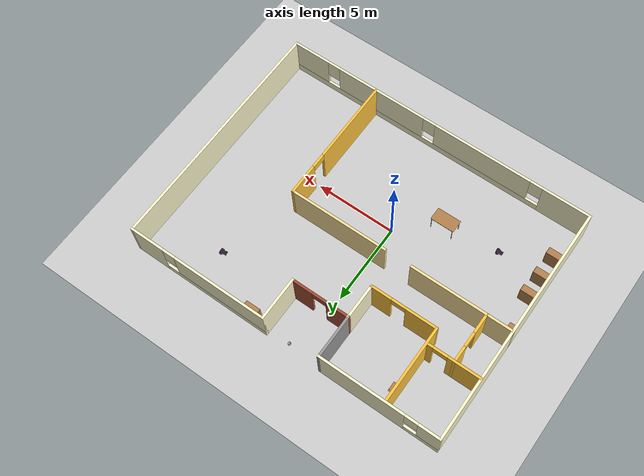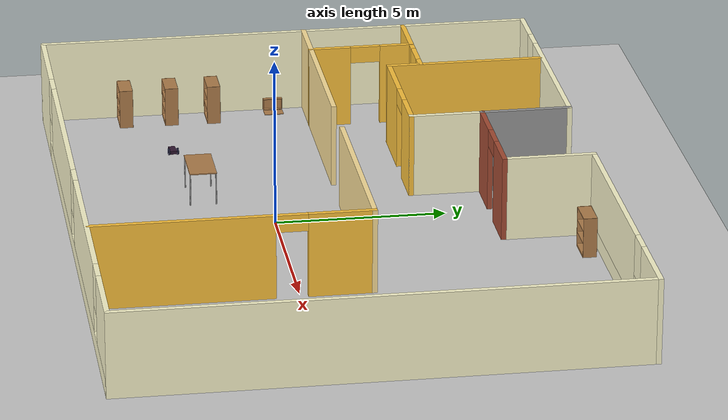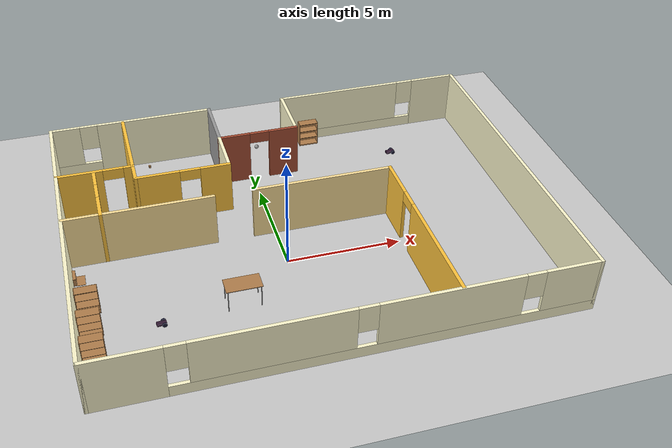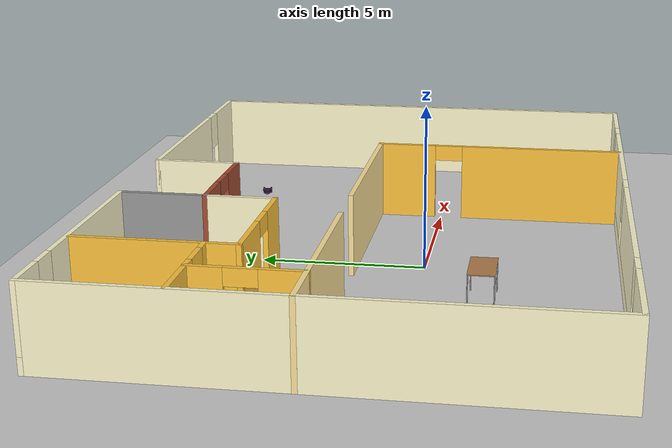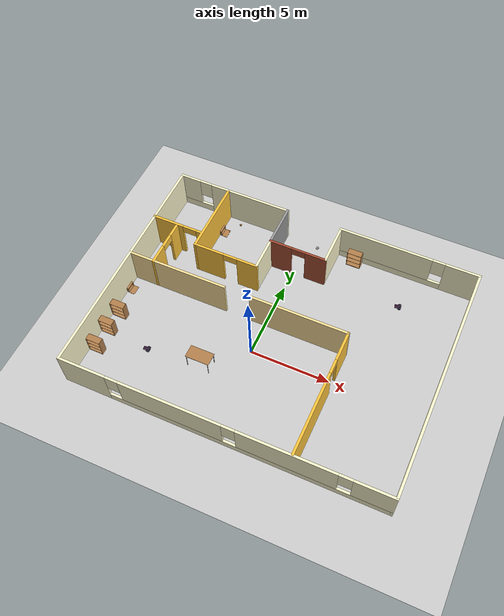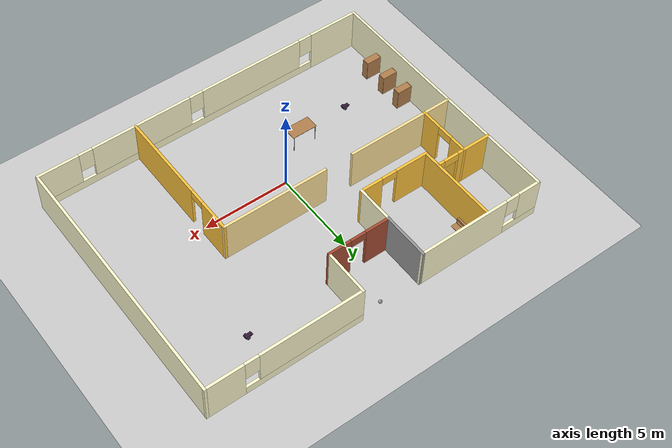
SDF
<sdf version="1.6">
 <world name="default">
  <plugin name="welcome" filename="libwelcome.so"/>
  <light name="sun" type="directional">
   <pose>0 0 10 0 -0 0</pose>
   <diffuse>0.8 0.8 0.8 1</diffuse>
   <specular>0.2 0.2 0.2 1</specular>
   <attenuation>
    <range>1000</range>
    <constant>0.9</constant>
    <linear>0.01</linear>
    <quadratic>0.001</quadratic>
   </attenuation>
   <direction>-0.5 0.1 -0.9</direction>
  </light>
  <model name="ground_plane">
   <static>1</static>
   <link name="link">
    <collision name="collision">
     <geometry><plane><normal>0 0 1</normal><size>100 100</size></plane></geometry>
     <surface><friction><ode><mu>100</mu><mu2>50</mu2></ode></friction></surface>
    </collision>
    <visual name="visual">
     <cast_shadows>0</cast_shadows>
     <geometry><plane><normal>0 0 1</normal><size>100 100</size></plane></geometry>
     <material>
      <script><uri>file://media/materials/scripts/gazebo.material</uri><name>Gazebo/Grey</name></script>
     </material>
    </visual>
   </link>
  </model>
  <gravity>0 0 -9.8</gravity>
  <magnetic_field>6e-06 2.3e-05 -4.2e-05</magnetic_field>
  <atmosphere type="adiabatic"/>
  <physics name="default_physics" default="0" type="ode">
   <max_step_size>0.001</max_step_size>
   <real_time_factor>1</real_time_factor>
   <real_time_update_rate>1000</real_time_update_rate>
  </physics>
  <scene><ambient>0.4 0.4 0.4 1</ambient><background>0.7 0.7 0.7 1</background><shadows>1</shadows></scene>
  <spherical_coordinates>
   <surface_model>EARTH_WGS84</surface_model>
   <latitude_deg>0</latitude_deg>
   <longitude_deg>0</longitude_deg>
   <elevation>0</elevation>
   <heading_deg>0</heading_deg>
  </spherical_coordinates>
  <model name="myHouse">
   <pose>1 1.5 0 0 -0 0</pose>
   <link name="Wall_10">
    <pose>-6.22482 7.425 0 0 -0 3.14159</pose>
    <visual name="Wall_10_Visual_0">
     <pose>-1.08871 0 1.25 0 -0 0</pose>
     <geometry><box><size>5.37259 0.15 2.5</size></box></geometry>
     <material>
      <script><uri>file://media/materials/scripts/gazebo.material</uri><name>Gazebo/Grey</name></script>
      <ambient>1 0.980392 0.811765 1</ambient>
     </material>
     <meta><layer>0</layer></meta>
    </visual>
    <collision name="Wall_10_Collision_0">
     <geometry><box><size>5.37259 0.15 2.5</size></box></geometry>
     <pose>-1.08871 0 1.25 0 -0 0</pose>
    </collision>
    <visual name="Wall_10_Visual_1">
     <pose>2.68629 0 0.25 0 -0 0</pose>
     <geometry><box><size>2.17741 0.15 0.5</size></box></geometry>
     <material>
      <script><uri>file://media/materials/scripts/gazebo.material</uri><name>Gazebo/Grey</name></script>
      <ambient>1 0.980392 0.811765 1</ambient>
     </material>
     <meta><layer>0</layer></meta>
    </visual>
    <collision name="Wall_10_Collision_1">
     <geometry><box><size>2.17741 0.15 0.5</size></box></geometry>
     <pose>2.68629 0 0.25 0 -0 0</pose>
    </collision>
    <visual name="Wall_10_Visual_2">
     <pose>3.08629 0 1.5 0 -0 0</pose>
     <geometry><box><size>1.37741 0.15 2</size></box></geometry>
     <material>
      <script><uri>file://media/materials/scripts/gazebo.material</uri><name>Gazebo/Grey</name></script>
      <ambient>1 0.980392 0.811765 1</ambient>
     </material>
     <meta><layer>0</layer></meta>
    </visual>
    <collision name="Wall_10_Collision_2">
     <geometry><box><size>1.37741 0.15 2</size></box></geometry>
     <pose>3.08629 0 1.5 0 -0 0</pose>
    </collision>
    <visual name="Wall_10_Visual_3">
     <pose>1.99759 0 1.9 0 -0 0</pose>
     <geometry><box><size>0.8 0.15 1.2</size></box></geometry>
     <material>
      <script><uri>file://media/materials/scripts/gazebo.material</uri><name>Gazebo/Grey</name></script>
      <ambient>1 0.980392 0.811765 1</ambient>
     </material>
     <meta><layer>0</layer></meta>
    </visual>
    <collision name="Wall_10_Collision_3">
     <geometry><box><size>0.8 0.15 1.2</size></box></geometry>
     <pose>1.99759 0 1.9 0 -0 0</pose>
    </collision>
   </link>
   <link name="Wall_12">
    <collision name="Wall_12_Collision">
     <geometry><box><size>2.25 0.15 2.5</size></box></geometry>
     <pose>0 0 1.25 0 -0 0</pose>
    </collision>
    <visual name="Wall_12_Visual">
     <pose>0 0 1.25 0 -0 0</pose>
     <geometry><box><size>2.25 0.15 2.5</size></box></geometry>
     <material>
      <script><uri>file://media/materials/scripts/gazebo.material</uri><name>Gazebo/Grey</name></script>
      <ambient>1 0.980392 0.811765 1</ambient>
     </material>
     <meta><layer>0</layer></meta>
    </visual>
    <pose>-2.52482 3.775 0 0 0 -1.5708</pose>
   </link>
   <link name="Wall_13">
    <pose>-4.57482 2.725 0 0 -0 3.14159</pose>
    <visual name="Wall_13_Visual_0">
     <pose>-1.44542 0 1.25 0 -0 0</pose>
     <geometry><box><size>1.35916 0.15 2.5</size></box></geometry>
     <material>
      <script><uri>file://media/materials/scripts/gazebo.material</uri><name>Gazebo/Grey</name></script>
      <ambient>1 0.772549 0.239216 1</ambient>
     </material>
     <meta><layer>0</layer></meta>
    </visual>
    <collision name="Wall_13_Collision_0">
     <geometry><box><size>1.35916 0.15 2.5</size></box></geometry>
     <pose>-1.44542 0 1.25 0 -0 0</pose>
    </collision>
    <visual name="Wall_13_Visual_1">
     <pose>1.12958 0 1.25 0 -0 0</pose>
     <geometry><box><size>1.99084 0.15 2.5</size></box></geometry>
     <material>
      <script><uri>file://media/materials/scripts/gazebo.material</uri><name>Gazebo/Grey</name></script>
      <ambient>1 0.772549 0.239216 1</ambient>
     </material>
     <meta><layer>0</layer></meta>
    </visual>
    <collision name="Wall_13_Collision_1">
     <geometry><box><size>1.99084 0.15 2.5</size></box></geometry>
     <pose>1.12958 0 1.25 0 -0 0</pose>
    </collision>
    <visual name="Wall_13_Visual_2">
     <pose>-0.315843 0 2.25 0 -0 0</pose>
     <geometry><box><size>0.9 0.15 0.5</size></box></geometry>
     <material>
      <script><uri>file://media/materials/scripts/gazebo.material</uri><name>Gazebo/Grey</name></script>
      <ambient>1 0.772549 0.239216 1</ambient>
     </material>
     <meta><layer>0</layer></meta>
    </visual>
    <collision name="Wall_13_Collision_2">
     <geometry><box><size>0.9 0.15 0.5</size></box></geometry>
     <pose>-0.315843 0 2.25 0 -0 0</pose>
    </collision>
   </link>
   <link name="Wall_14">
    <collision name="Wall_14_Collision">
     <geometry><box><size>4.75 0.15 2.5</size></box></geometry>
     <pose>0 0 1.25 0 -0 0</pose>
    </collision>
    <visual name="Wall_14_Visual">
     <pose>0 0 1.25 0 -0 0</pose>
     <geometry><box><size>4.75 0.15 2.5</size></box></geometry>
     <material>
      <script><uri>file://media/materials/scripts/gazebo.material</uri><name>Gazebo/Grey</name></script>
      <ambient>1 0.772549 0.239216 1</ambient>
     </material>
     <meta><layer>0</layer></meta>
    </visual>
    <pose>-6.62481 5.025 0 0 -0 1.5708</pose>
   </link>
   <link name="Wall_16">
    <pose>-8.26166 3.67479 0 0 -0 0</pose>
    <visual name="Wall_16_Visual_0">
     <pose>-0.692622 0 1.25 0 -0 0</pose>
     <geometry><box><size>2.03776 0.15 2.5</size></box></geometry>
     <material>
      <script><uri>file://media/materials/scripts/gazebo.material</uri><name>Gazebo/Grey</name></script>
      <ambient>1 0.772549 0.239216 1</ambient>
     </material>
     <meta><layer>0</layer></meta>
    </visual>
    <collision name="Wall_16_Collision_0">
     <geometry><box><size>2.03776 0.15 2.5</size></box></geometry>
     <pose>-0.692622 0 1.25 0 -0 0</pose>
    </collision>
    <visual name="Wall_16_Visual_1">
     <pose>1.46888 0 1.25 0 -0 0</pose>
     <geometry><box><size>0.485244 0.15 2.5</size></box></geometry>
     <material>
      <script><uri>file://media/materials/scripts/gazebo.material</uri><name>Gazebo/Grey</name></script>
      <ambient>1 0.772549 0.239216 1</ambient>
     </material>
     <meta><layer>0</layer></meta>
    </visual>
    <collision name="Wall_16_Collision_1">
     <geometry><box><size>0.485244 0.15 2.5</size></box></geometry>
     <pose>1.46888 0 1.25 0 -0 0</pose>
    </collision>
    <visual name="Wall_16_Visual_2">
     <pose>0.776256 0 2.25 0 -0 0</pose>
     <geometry><box><size>0.9 0.15 0.5</size></box></geometry>
     <material>
      <script><uri>file://media/materials/scripts/gazebo.material</uri><name>Gazebo/Grey</name></script>
      <ambient>1 0.772549 0.239216 1</ambient>
     </material>
     <meta><layer>0</layer></meta>
    </visual>
    <collision name="Wall_16_Collision_2">
     <geometry><box><size>0.9 0.15 0.5</size></box></geometry>
     <pose>0.776256 0 2.25 0 -0 0</pose>
    </collision>
   </link>
   <link name="Wall_21">
    <pose>4.20181 -3.38793 0 0 0 -1.5708</pose>
    <visual name="Wall_21_Visual_0">
     <pose>-3.08247 0 1.25 0 -0 0</pose>
     <geometry><box><size>1.94451 0.15 2.5</size></box></geometry>
     <material>
      <script><uri>file://media/materials/scripts/gazebo.material</uri><name>Gazebo/Grey</name></script>
      <ambient>1 0.772549 0.239216 1</ambient>
     </material>
     <meta><layer>0</layer></meta>
    </visual>
    <collision name="Wall_21_Collision_0">
     <geometry><box><size>1.94451 0.15 2.5</size></box></geometry>
     <pose>-3.08247 0 1.25 0 -0 0</pose>
    </collision>
    <visual name="Wall_21_Visual_1">
     <pose>1.42226 0 1.25 0 -0 0</pose>
     <geometry><box><size>5.26493 0.15 2.5</size></box></geometry>
     <material>
      <script><uri>file://media/materials/scripts/gazebo.material</uri><name>Gazebo/Grey</name></script>
      <ambient>1 0.772549 0.239216 1</ambient>
     </material>
     <meta><layer>0</layer></meta>
    </visual>
    <collision name="Wall_21_Collision_1">
     <geometry><box><size>5.26493 0.15 2.5</size></box></geometry>
     <pose>1.42226 0 1.25 0 -0 0</pose>
    </collision>
    <visual name="Wall_21_Visual_2">
     <pose>-1.66021 0 2.25 0 -0 0</pose>
     <geometry><box><size>0.9 0.15 0.5</size></box></geometry>
     <material>
      <script><uri>file://media/materials/scripts/gazebo.material</uri><name>Gazebo/Grey</name></script>
      <ambient>1 0.772549 0.239216 1</ambient>
     </material>
     <meta><layer>0</layer></meta>
    </visual>
    <collision name="Wall_21_Collision_2">
     <geometry><box><size>0.9 0.15 0.5</size></box></geometry>
     <pose>-1.66021 0 2.25 0 -0 0</pose>
    </collision>
   </link>
   <link name="Wall_23">
    <pose>-8.33016 2.13129 0 0 0 -1.5708</pose>
    <visual name="Wall_23_Visual_0">
     <pose>-1.09422 0 1.25 0 -0 0</pose>
     <geometry><box><size>1.0487 0.15 2.5</size></box></geometry>
     <material>
      <script><uri>file://media/materials/scripts/gazebo.material</uri><name>Gazebo/Grey</name></script>
      <ambient>1 0.772549 0.239216 1</ambient>
     </material>
     <meta><layer>0</layer></meta>
    </visual>
    <collision name="Wall_23_Collision_0">
     <geometry><box><size>1.0487 0.15 2.5</size></box></geometry>
     <pose>-1.09422 0 1.25 0 -0 0</pose>
    </collision>
    <visual name="Wall_23_Visual_1">
     <pose>0.974348 0 1.25 0 -0 0</pose>
     <geometry><box><size>1.28844 0.15 2.5</size></box></geometry>
     <material>
      <script><uri>file://media/materials/scripts/gazebo.material</uri><name>Gazebo/Grey</name></script>
      <ambient>1 0.772549 0.239216 1</ambient>
     </material>
     <meta><layer>0</layer></meta>
    </visual>
    <collision name="Wall_23_Collision_1">
     <geometry><box><size>1.28844 0.15 2.5</size></box></geometry>
     <pose>0.974348 0 1.25 0 -0 0</pose>
    </collision>
    <visual name="Wall_23_Visual_2">
     <pose>-0.119873 0 2.25 0 -0 0</pose>
     <geometry><box><size>0.9 0.15 0.5</size></box></geometry>
     <material>
      <script><uri>file://media/materials/scripts/gazebo.material</uri><name>Gazebo/Grey</name></script>
      <ambient>1 0.772549 0.239216 1</ambient>
     </material>
     <meta><layer>0</layer></meta>
    </visual>
    <collision name="Wall_23_Collision_2">
     <geometry><box><size>0.9 0.15 0.5</size></box></geometry>
     <pose>-0.119873 0 2.25 0 -0 0</pose>
    </collision>
   </link>
   <link name="Wall_25">
    <collision name="Wall_25_Collision">
     <geometry><box><size>6.43405 0.15 2.5</size></box></geometry>
     <pose>0 0 1.25 0 -0 0</pose>
    </collision>
    <visual name="Wall_25_Visual">
     <pose>0 0 1.25 0 -0 0</pose>
     <geometry><box><size>6.43405 0.15 2.5</size></box></geometry>
     <material>
      <script><uri>file://media/materials/scripts/gazebo.material</uri><name>Gazebo/Grey</name></script>
      <ambient>1 0.890196 0.607843 1</ambient>
     </material>
     <meta><layer>0</layer></meta>
    </visual>
    <pose>-6.78316 0.591794 0 0 -0 0</pose>
   </link>
   <link name="Wall_27">
    <collision name="Wall_27_Collision">
     <geometry><box><size>6.25 0.15 2.5</size></box></geometry>
     <pose>0 0 1.25 0 -0 0</pose>
    </collision>
    <visual name="Wall_27_Visual">
     <pose>0 0 1.25 0 -0 0</pose>
     <geometry><box><size>6.25 0.15 2.5</size></box></geometry>
     <material>
      <script><uri>file://media/materials/scripts/gazebo.material</uri><name>Gazebo/Grey</name></script>
      <ambient>1 0.890196 0.607843 1</ambient>
     </material>
     <meta><layer>0</layer></meta>
    </visual>
    <pose>1.15184 0.591794 0 0 -0 3.14159</pose>
   </link>
   <link name="Wall_3">
    <collision name="Wall_3_Collision">
     <geometry><box><size>15 0.15 2.5</size></box></geometry>
     <pose>0 0 1.25 0 -0 0</pose>
    </collision>
    <visual name="Wall_3_Visual">
     <pose>0 0 1.25 0 -0 0</pose>
     <geometry><box><size>15 0.15 2.5</size></box></geometry>
     <material>
      <script><uri>file://media/materials/scripts/gazebo.material</uri><name>Gazebo/Grey</name></script>
      <ambient>1 0.980392 0.811765 1</ambient>
     </material>
     <meta><layer>0</layer></meta>
    </visual>
    <pose>-9.92482 0 0 0 0 -1.5708</pose>
   </link>
   <link name="Wall_4">
    <pose>0.000185 -7.425 0 0 -0 0</pose>
    <visual name="Wall_4_Visual_0">
     <pose>-8.48669 0 1.25 0 -0 0</pose>
     <geometry><box><size>3.02663 0.15 2.5</size></box></geometry>
     <material>
      <script><uri>file://media/materials/scripts/gazebo.material</uri><name>Gazebo/Grey</name></script>
      <ambient>1 0.980392 0.811765 1</ambient>
     </material>
     <meta><layer>0</layer></meta>
    </visual>
    <collision name="Wall_4_Collision_0">
     <geometry><box><size>3.02663 0.15 2.5</size></box></geometry>
     <pose>-8.48669 0 1.25 0 -0 0</pose>
    </collision>
    <visual name="Wall_4_Visual_1">
     <pose>1.51331 0 0.25 0 -0 0</pose>
     <geometry><box><size>16.9734 0.15 0.5</size></box></geometry>
     <material>
      <script><uri>file://media/materials/scripts/gazebo.material</uri><name>Gazebo/Grey</name></script>
      <ambient>1 0.980392 0.811765 1</ambient>
     </material>
     <meta><layer>0</layer></meta>
    </visual>
    <collision name="Wall_4_Collision_1">
     <geometry><box><size>16.9734 0.15 0.5</size></box></geometry>
     <pose>1.51331 0 0.25 0 -0 0</pose>
    </collision>
    <visual name="Wall_4_Visual_2">
     <pose>-3.03555 0 1.5 0 -0 0</pose>
     <geometry><box><size>6.27565 0.15 2</size></box></geometry>
     <material>
      <script><uri>file://media/materials/scripts/gazebo.material</uri><name>Gazebo/Grey</name></script>
      <ambient>1 0.980392 0.811765 1</ambient>
     </material>
     <meta><layer>0</layer></meta>
    </visual>
    <collision name="Wall_4_Collision_2">
     <geometry><box><size>6.27565 0.15 2</size></box></geometry>
     <pose>-3.03555 0 1.5 0 -0 0</pose>
    </collision>
    <visual name="Wall_4_Visual_3">
     <pose>3.8406 0 1.5 0 -0 0</pose>
     <geometry><box><size>5.87665 0.15 2</size></box></geometry>
     <material>
      <script><uri>file://media/materials/scripts/gazebo.material</uri><name>Gazebo/Grey</name></script>
      <ambient>1 0.980392 0.811765 1</ambient>
     </material>
     <meta><layer>0</layer></meta>
    </visual>
    <collision name="Wall_4_Collision_3">
     <geometry><box><size>5.87665 0.15 2</size></box></geometry>
     <pose>3.8406 0 1.5 0 -0 0</pose>
    </collision>
    <visual name="Wall_4_Visual_4">
     <pose>8.78946 0 1.5 0 -0 0</pose>
     <geometry><box><size>2.42107 0.15 2</size></box></geometry>
     <material>
      <script><uri>file://media/materials/scripts/gazebo.material</uri><name>Gazebo/Grey</name></script>
      <ambient>1 0.980392 0.811765 1</ambient>
     </material>
     <meta><layer>0</layer></meta>
    </visual>
    <collision name="Wall_4_Collision_4">
     <geometry><box><size>2.42107 0.15 2</size></box></geometry>
     <pose>8.78946 0 1.5 0 -0 0</pose>
    </collision>
    <visual name="Wall_4_Visual_5">
     <pose>-6.57338 0 1.9 0 -0 0</pose>
     <geometry><box><size>0.8 0.15 1.2</size></box></geometry>
     <material>
      <script><uri>file://media/materials/scripts/gazebo.material</uri><name>Gazebo/Grey</name></script>
      <ambient>1 0.980392 0.811765 1</ambient>
     </material>
     <meta><layer>0</layer></meta>
    </visual>
    <collision name="Wall_4_Collision_5">
     <geometry><box><size>0.8 0.15 1.2</size></box></geometry>
     <pose>-6.57338 0 1.9 0 -0 0</pose>
    </collision>
    <visual name="Wall_4_Visual_6">
     <pose>0.502278 0 1.9 0 -0 0</pose>
     <geometry><box><size>0.8 0.15 1.2</size></box></geometry>
     <material>
      <script><uri>file://media/materials/scripts/gazebo.material</uri><name>Gazebo/Grey</name></script>
      <ambient>1 0.980392 0.811765 1</ambient>
     </material>
     <meta><layer>0</layer></meta>
    </visual>
    <collision name="Wall_4_Collision_6">
     <geometry><box><size>0.8 0.15 1.2</size></box></geometry>
     <pose>0.502278 0 1.9 0 -0 0</pose>
    </collision>
    <visual name="Wall_4_Visual_7">
     <pose>7.17893 0 1.9 0 -0 0</pose>
     <geometry><box><size>0.8 0.15 1.2</size></box></geometry>
     <material>
      <script><uri>file://media/materials/scripts/gazebo.material</uri><name>Gazebo/Grey</name></script>
      <ambient>1 0.980392 0.811765 1</ambient>
     </material>
     <meta><layer>0</layer></meta>
    </visual>
    <collision name="Wall_4_Collision_7">
     <geometry><box><size>0.8 0.15 1.2</size></box></geometry>
     <pose>7.17893 0 1.9 0 -0 0</pose>
    </collision>
   </link>
   <link name="Wall_5">
    <collision name="Wall_5_Collision">
     <geometry><box><size>15 0.15 2.5</size></box></geometry>
     <pose>0 0 1.25 0 -0 0</pose>
    </collision>
    <visual name="Wall_5_Visual">
     <pose>0 0 1.25 0 -0 0</pose>
     <geometry><box><size>15 0.15 2.5</size></box></geometry>
     <material>
      <script><uri>file://media/materials/scripts/gazebo.material</uri><name>Gazebo/Grey</name></script>
      <ambient>1 0.980392 0.811765 1</ambient>
     </material>
     <meta><layer>0</layer></meta>
    </visual>
    <pose>9.92519 0 0 0 -0 1.5708</pose>
   </link>
   <link name="Wall_6">
    <pose>5.50019 7.425 0 0 -0 3.14159</pose>
    <visual name="Wall_6_Visual_0">
     <pose>-3.39587 0 1.25 0 -0 0</pose>
     <geometry><box><size>2.20827 0.15 2.5</size></box></geometry>
     <material>
      <script><uri>file://media/materials/scripts/gazebo.material</uri><name>Gazebo/Grey</name></script>
      <ambient>1 0.980392 0.811765 1</ambient>
     </material>
     <meta><layer>0</layer></meta>
    </visual>
    <collision name="Wall_6_Collision_0">
     <geometry><box><size>2.20827 0.15 2.5</size></box></geometry>
     <pose>-3.39587 0 1.25 0 -0 0</pose>
    </collision>
    <visual name="Wall_6_Visual_1">
     <pose>1.10414 0 0.25 0 -0 0</pose>
     <geometry><box><size>6.79173 0.15 0.5</size></box></geometry>
     <material>
      <script><uri>file://media/materials/scripts/gazebo.material</uri><name>Gazebo/Grey</name></script>
      <ambient>1 0.980392 0.811765 1</ambient>
     </material>
     <meta><layer>0</layer></meta>
    </visual>
    <collision name="Wall_6_Collision_1">
     <geometry><box><size>6.79173 0.15 0.5</size></box></geometry>
     <pose>1.10414 0 0.25 0 -0 0</pose>
    </collision>
    <visual name="Wall_6_Visual_2">
     <pose>1.50413 0 1.5 0 -0 0</pose>
     <geometry><box><size>5.99173 0.15 2</size></box></geometry>
     <material>
      <script><uri>file://media/materials/scripts/gazebo.material</uri><name>Gazebo/Grey</name></script>
      <ambient>1 0.980392 0.811765 1</ambient>
     </material>
     <meta><layer>0</layer></meta>
    </visual>
    <collision name="Wall_6_Collision_2">
     <geometry><box><size>5.99173 0.15 2</size></box></geometry>
     <pose>1.50413 0 1.5 0 -0 0</pose>
    </collision>
    <visual name="Wall_6_Visual_3">
     <pose>-1.89173 0 1.9 0 -0 0</pose>
     <geometry><box><size>0.8 0.15 1.2</size></box></geometry>
     <material>
      <script><uri>file://media/materials/scripts/gazebo.material</uri><name>Gazebo/Grey</name></script>
      <ambient>1 0.980392 0.811765 1</ambient>
     </material>
     <meta><layer>0</layer></meta>
    </visual>
    <collision name="Wall_6_Collision_3">
     <geometry><box><size>0.8 0.15 1.2</size></box></geometry>
     <pose>-1.89173 0 1.9 0 -0 0</pose>
    </collision>
   </link>
   <link name="Wall_7">
    <collision name="Wall_7_Collision">
     <geometry><box><size>2.75 0.15 2.5</size></box></geometry>
     <pose>0 0 1.25 0 -0 0</pose>
    </collision>
    <visual name="Wall_7_Visual">
     <pose>0 0 1.25 0 -0 0</pose>
     <geometry><box><size>2.75 0.15 2.5</size></box></geometry>
     <material>
      <script><uri>file://media/materials/scripts/gazebo.material</uri><name>Gazebo/Grey</name></script>
      <ambient>1 0.980392 0.811765 1</ambient>
     </material>
     <meta><layer>0</layer></meta>
    </visual>
    <pose>1.07519 6.125 0 0 0 -1.5708</pose>
   </link>
   <link name="Wall_8">
    <pose>-0.724815 4.825 0 0 -0 3.14159</pose>
    <visual name="Wall_8_Visual_0">
     <pose>-1.19094 0 1.25 0 -0 0</pose>
     <geometry><box><size>1.36813 0.15 2.5</size></box></geometry>
     <material>
      <script><uri>file://media/materials/scripts/gazebo.material</uri><name>Gazebo/Bricks</name></script>
      <ambient>1 1 1 1</ambient>
     </material>
     <meta><layer>0</layer></meta>
    </visual>
    <collision name="Wall_8_Collision_0">
     <geometry><box><size>1.36813 0.15 2.5</size></box></geometry>
     <pose>-1.19094 0 1.25 0 -0 0</pose>
    </collision>
    <visual name="Wall_8_Visual_1">
     <pose>1.13407 0 1.25 0 -0 0</pose>
     <geometry><box><size>1.48187 0.15 2.5</size></box></geometry>
     <material>
      <script><uri>file://media/materials/scripts/gazebo.material</uri><name>Gazebo/Bricks</name></script>
      <ambient>1 1 1 1</ambient>
     </material>
     <meta><layer>0</layer></meta>
    </visual>
    <collision name="Wall_8_Collision_1">
     <geometry><box><size>1.48187 0.15 2.5</size></box></geometry>
     <pose>1.13407 0 1.25 0 -0 0</pose>
    </collision>
    <visual name="Wall_8_Visual_2">
     <pose>-0.056869 0 2.25 0 -0 0</pose>
     <geometry><box><size>0.9 0.15 0.5</size></box></geometry>
     <material>
      <script><uri>file://media/materials/scripts/gazebo.material</uri><name>Gazebo/Bricks</name></script>
      <ambient>1 1 1 1</ambient>
     </material>
     <meta><layer>0</layer></meta>
    </visual>
    <collision name="Wall_8_Collision_2">
     <geometry><box><size>0.9 0.15 0.5</size></box></geometry>
     <pose>-0.056869 0 2.25 0 -0 0</pose>
    </collision>
   </link>
   <link name="Wall_9">
    <collision name="Wall_9_Collision">
     <geometry><box><size>2.75 0.15 2.5</size></box></geometry>
     <pose>0 0 1.25 0 -0 0</pose>
    </collision>
    <visual name="Wall_9_Visual">
     <pose>0 0 1.25 0 -0 0</pose>
     <geometry><box><size>2.75 0.15 2.5</size></box></geometry>
     <material>
      <script><uri>file://media/materials/scripts/gazebo.material</uri><name>Gazebo/Grey</name></script>
      <ambient>1 1 1 1</ambient>
     </material>
     <meta><layer>0</layer></meta>
    </visual>
    <pose>-2.52482 6.125 0 0 -0 1.5708</pose>
   </link>
   <static>1</static>
  </model>
  <model name="myMobileRobot">
   <static>0</static>
   <link name="chassis">
    <pose>0 0 0.1 0 -0 0</pose>
    <collision name="collision"><geometry><box><size>0.4 0.2 0.1</size></box></geometry></collision>
    <visual name="visual">
     <geometry><box><size>0.4 0.2 0.1</size></box></geometry>
     <material>
      <ambient>0.2 0.1 0.1 1</ambient>
      <diffuse>0.2 0.1 0.2 1</diffuse>
      <specular>0 0 0 0</specular>
      <emissive>0 0 0 1</emissive>
     </material>
    </visual>
    <collision name="caster_collision">
     <pose>-0.15 0 -0.05 0 -0 0</pose>
     <geometry><sphere><radius>0.05</radius></sphere></geometry>
     <surface><friction><ode><mu>0</mu><mu2>0</mu2><slip1>1</slip1><slip2>1</slip2></ode></friction></surface>
    </collision>
    <visual name="caster_visual">
     <pose>-0.15 0 -0.05 0 -0 0</pose>
     <geometry><sphere><radius>0.05</radius></sphere></geometry>
    </visual>
    <inertial>
     <inertia><ixx>1</ixx><ixy>0</ixy><ixz>0</ixz><iyy>1</iyy><iyz>0</iyz><izz>1</izz></inertia>
     <mass>1</mass>
    </inertial>
   </link>
   <link name="left_wheel">
    <pose>0.1 0.13 0.1 -0 1.5707 1.5707</pose>
    <collision name="collision">
     <geometry><cylinder><radius>0.1</radius><length>0.05</length></cylinder></geometry>
    </collision>
    <visual name="visual">
     <geometry><cylinder><radius>0.1</radius><length>0.05</length></cylinder></geometry>
     <material>
      <ambient>0.1 0.1 0.1 1</ambient>
      <diffuse>0.1 0.1 0.2 1</diffuse>
      <specular>0 0 0 0</specular>
      <emissive>0 0 0 1</emissive>
     </material>
    </visual>
    <inertial>
     <inertia><ixx>1</ixx><ixy>0</ixy><ixz>0</ixz><iyy>1</iyy><iyz>0</iyz><izz>1</izz></inertia>
     <mass>1</mass>
    </inertial>
   </link>
   <link name="right_wheel">
    <pose>0.1 -0.13 0.1 -0 1.5707 1.5707</pose>
    <collision name="collision">
     <geometry><cylinder><radius>0.1</radius><length>0.05</length></cylinder></geometry>
    </collision>
    <visual name="visual">
     <geometry><cylinder><radius>0.1</radius><length>0.05</length></cylinder></geometry>
     <material>
      <ambient>0.1 0.1 0.1 1</ambient>
      <diffuse>0.1 0.1 0.2 1</diffuse>
      <specular>0 0 0 0</specular>
      <emissive>0 0 0 1</emissive>
     </material>
    </visual>
    <inertial>
     <inertia><ixx>1</ixx><ixy>0</ixy><ixz>0</ixz><iyy>1</iyy><iyz>0</iyz><izz>1</izz></inertia>
     <mass>1</mass>
    </inertial>
   </link>
   <joint name="left_wheel_hinge" type="revolute">
    <pose>0 0 -0.03 0 -0 0</pose>
    <child>left_wheel</child>
    <parent>chassis</parent>
    <axis>
     <xyz>0 1 0</xyz>
     <use_parent_model_frame>1</use_parent_model_frame>
     <limit><lower>-1e+16</lower><upper>1e+16</upper></limit>
     <dynamics><spring_reference>0</spring_reference><spring_stiffness>0</spring_stiffness></dynamics>
    </axis>
   </joint>
   <joint name="right_wheel_hinge" type="revolute">
    <pose>0 0 0.03 0 -0 0</pose>
    <child>right_wheel</child>
    <parent>chassis</parent>
    <axis>
     <xyz>0 1 0</xyz>
     <use_parent_model_frame>1</use_parent_model_frame>
     <limit><lower>-1e+16</lower><upper>1e+16</upper></limit>
     <dynamics><spring_reference>0</spring_reference><spring_stiffness>0</spring_stiffness></dynamics>
    </axis>
   </joint>
   <pose>-5.70362 -2.35124 6e-06 9e-06 4.4e-05 0.075311</pose>
  </model>
  <model name="table">
   <static>1</static>
   <link name="link">
    <collision name="surface">
     <pose>0 0 1 0 -0 0</pose>
     <geometry><box><size>1.5 0.8 0.03</size></box></geometry>
     <surface><friction><ode><mu>0.6</mu><mu2>0.6</mu2></ode></friction></surface>
    </collision>
    <visual name="visual1">
     <pose>0 0 1 0 -0 0</pose>
     <geometry><box><size>1.5 0.8 0.03</size></box></geometry>
     <material>
      <script><uri>file://media/materials/scripts/gazebo.material</uri><name>Gazebo/Wood</name></script>
     </material>
    </visual>
    <collision name="front_left_leg">
     <pose>0.68 0.38 0.5 0 -0 0</pose>
     <geometry><cylinder><radius>0.02</radius><length>1</length></cylinder></geometry>
    </collision>
    <visual name="front_left_leg">
     <pose>0.68 0.38 0.5 0 -0 0</pose>
     <geometry><cylinder><radius>0.02</radius><length>1</length></cylinder></geometry>
     <material>
      <script><uri>file://media/materials/scripts/gazebo.material</uri><name>Gazebo/Grey</name></script>
     </material>
    </visual>
    <collision name="front_right_leg">
     <pose>0.68 -0.38 0.5 0 -0 0</pose>
     <geometry><cylinder><radius>0.02</radius><length>1</length></cylinder></geometry>
    </collision>
    <visual name="front_right_leg">
     <pose>0.68 -0.38 0.5 0 -0 0</pose>
     <geometry><cylinder><radius>0.02</radius><length>1</length></cylinder></geometry>
     <material>
      <script><uri>file://media/materials/scripts/gazebo.material</uri><name>Gazebo/Grey</name></script>
     </material>
    </visual>
    <collision name="back_right_leg">
     <pose>-0.68 -0.38 0.5 0 -0 0</pose>
     <geometry><cylinder><radius>0.02</radius><length>1</length></cylinder></geometry>
    </collision>
    <visual name="back_right_leg">
     <pose>-0.68 -0.38 0.5 0 -0 0</pose>
     <geometry><cylinder><radius>0.02</radius><length>1</length></cylinder></geometry>
     <material>
      <script><uri>file://media/materials/scripts/gazebo.material</uri><name>Gazebo/Grey</name></script>
     </material>
    </visual>
    <collision name="back_left_leg">
     <pose>-0.68 0.38 0.5 0 -0 0</pose>
     <geometry><cylinder><radius>0.02</radius><length>1</length></cylinder></geometry>
    </collision>
    <visual name="back_left_leg">
     <pose>-0.68 0.38 0.5 0 -0 0</pose>
     <geometry><cylinder><radius>0.02</radius><length>1</length></cylinder></geometry>
     <material>
      <script><uri>file://media/materials/scripts/gazebo.material</uri><name>Gazebo/Grey</name></script>
     </material>
    </visual>
   </link>
   <pose>-2.33152 -1.90169 0 0 -0 0</pose>
  </model>
  <model name="bookshelf">
   <static>1</static>
   <link name="link">
    <inertial><mass>1</mass></inertial>
    <collision name="back">
     <pose>0 0.005 0.6 0 -0 0</pose>
     <geometry><box><size>0.9 0.01 1.2</size></box></geometry>
    </collision>
    <visual name="visual1">
     <pose>0 0.005 0.6 0 -0 0</pose>
     <geometry><box><size>0.9 0.01 1.2</size></box></geometry>
     <material>
      <script><uri>file://media/materials/scripts/gazebo.material</uri><name>Gazebo/Wood</name></script>
     </material>
    </visual>
    <collision name="left_side">
     <pose>0.45 -0.195 0.6 0 -0 0</pose>
     <geometry><box><size>0.02 0.4 1.2</size></box></geometry>
    </collision>
    <visual name="visual2">
     <pose>0.45 -0.195 0.6 0 -0 0</pose>
     <geometry><box><size>0.02 0.4 1.2</size></box></geometry>
     <material>
      <script><uri>file://media/materials/scripts/gazebo.material</uri><name>Gazebo/Wood</name></script>
     </material>
    </visual>
    <collision name="right_side">
     <pose>-0.45 -0.195 0.6 0 -0 0</pose>
     <geometry><box><size>0.02 0.4 1.2</size></box></geometry>
    </collision>
    <visual name="visual3">
     <pose>-0.45 -0.195 0.6 0 -0 0</pose>
     <geometry><box><size>0.02 0.4 1.2</size></box></geometry>
     <material>
      <script><uri>file://media/materials/scripts/gazebo.material</uri><name>Gazebo/Wood</name></script>
     </material>
    </visual>
    <collision name="bottom">
     <pose>0 -0.195 0.03 0 -0 0</pose>
     <geometry><box><size>0.88 0.4 0.06</size></box></geometry>
    </collision>
    <visual name="visual4">
     <pose>0 -0.195 0.03 0 -0 0</pose>
     <geometry><box><size>0.88 0.4 0.06</size></box></geometry>
     <material>
      <script><uri>file://media/materials/scripts/gazebo.material</uri><name>Gazebo/Wood</name></script>
     </material>
    </visual>
    <collision name="top">
     <pose>0 -0.195 1.19 0 -0 0</pose>
     <geometry><box><size>0.88 0.4 0.02</size></box></geometry>
    </collision>
    <visual name="visual5">
     <pose>0 -0.195 1.19 0 -0 0</pose>
     <geometry><box><size>0.88 0.4 0.02</size></box></geometry>
     <material>
      <script><uri>file://media/materials/scripts/gazebo.material</uri><name>Gazebo/Wood</name></script>
     </material>
    </visual>
    <collision name="low_shelf">
     <pose>0 -0.195 0.43 0 -0 0</pose>
     <geometry><box><size>0.88 0.4 0.02</size></box></geometry>
    </collision>
    <visual name="visual6">
     <pose>0 -0.195 0.43 0 -0 0</pose>
     <geometry><box><size>0.88 0.4 0.02</size></box></geometry>
     <material>
      <script><uri>file://media/materials/scripts/gazebo.material</uri><name>Gazebo/Wood</name></script>
     </material>
    </visual>
    <collision name="high_shelf">
     <pose>0 -0.195 0.8 0 -0 0</pose>
     <geometry><box><size>0.88 0.4 0.02</size></box></geometry>
    </collision>
    <visual name="visual7">
     <pose>0 -0.195 0.8 0 -0 0</pose>
     <geometry><box><size>0.88 0.4 0.02</size></box></geometry>
     <material>
      <script><uri>file://media/materials/scripts/gazebo.material</uri><name>Gazebo/Wood</name></script>
     </material>
    </visual>
   </link>
   <pose>3.29143 8.71258 0 0 -0 0</pose>
  </model>
  <model name="myMobileRobot_0">
   <static>0</static>
   <link name="chassis">
    <pose>0 0 0.1 0 -0 0</pose>
    <collision name="collision"><geometry><box><size>0.4 0.2 0.1</size></box></geometry></collision>
    <visual name="visual">
     <geometry><box><size>0.4 0.2 0.1</size></box></geometry>
     <material>
      <ambient>0.2 0.1 0.1 1</ambient>
      <diffuse>0.2 0.1 0.2 1</diffuse>
      <specular>0 0 0 0</specular>
      <emissive>0 0 0 1</emissive>
     </material>
    </visual>
    <collision name="caster_collision">
     <pose>-0.15 0 -0.05 0 -0 0</pose>
     <geometry><sphere><radius>0.05</radius></sphere></geometry>
     <surface><friction><ode><mu>0</mu><mu2>0</mu2><slip1>1</slip1><slip2>1</slip2></ode></friction></surface>
    </collision>
    <visual name="caster_visual">
     <pose>-0.15 0 -0.05 0 -0 0</pose>
     <geometry><sphere><radius>0.05</radius></sphere></geometry>
    </visual>
    <inertial>
     <inertia><ixx>1</ixx><ixy>0</ixy><ixz>0</ixz><iyy>1</iyy><iyz>0</iyz><izz>1</izz></inertia>
     <mass>1</mass>
    </inertial>
   </link>
   <link name="left_wheel">
    <pose>0.1 0.13 0.1 -0 1.5707 1.5707</pose>
    <collision name="collision">
     <geometry><cylinder><radius>0.1</radius><length>0.05</length></cylinder></geometry>
    </collision>
    <visual name="visual">
     <geometry><cylinder><radius>0.1</radius><length>0.05</length></cylinder></geometry>
     <material>
      <ambient>0.1 0.1 0.1 1</ambient>
      <diffuse>0.1 0.1 0.2 1</diffuse>
      <specular>0 0 0 0</specular>
      <emissive>0 0 0 1</emissive>
     </material>
    </visual>
    <inertial>
     <inertia><ixx>1</ixx><ixy>0</ixy><ixz>0</ixz><iyy>1</iyy><iyz>0</iyz><izz>1</izz></inertia>
     <mass>1</mass>
    </inertial>
   </link>
   <link name="right_wheel">
    <pose>0.1 -0.13 0.1 -0 1.5707 1.5707</pose>
    <collision name="collision">
     <geometry><cylinder><radius>0.1</radius><length>0.05</length></cylinder></geometry>
    </collision>
    <visual name="visual">
     <geometry><cylinder><radius>0.1</radius><length>0.05</length></cylinder></geometry>
     <material>
      <ambient>0.1 0.1 0.1 1</ambient>
      <diffuse>0.1 0.1 0.2 1</diffuse>
      <specular>0 0 0 0</specular>
      <emissive>0 0 0 1</emissive>
     </material>
    </visual>
    <inertial>
     <inertia><ixx>1</ixx><ixy>0</ixy><ixz>0</ixz><iyy>1</iyy><iyz>0</iyz><izz>1</izz></inertia>
     <mass>1</mass>
    </inertial>
   </link>
   <joint name="left_wheel_hinge" type="revolute">
    <pose>0 0 -0.03 0 -0 0</pose>
    <child>left_wheel</child>
    <parent>chassis</parent>
    <axis>
     <xyz>0 1 0</xyz>
     <use_parent_model_frame>1</use_parent_model_frame>
     <limit><lower>-1e+16</lower><upper>1e+16</upper></limit>
     <dynamics><spring_reference>0</spring_reference><spring_stiffness>0</spring_stiffness></dynamics>
    </axis>
   </joint>
   <joint name="right_wheel_hinge" type="revolute">
    <pose>0 0 0.03 0 -0 0</pose>
    <child>right_wheel</child>
    <parent>chassis</parent>
    <axis>
     <xyz>0 1 0</xyz>
     <use_parent_model_frame>1</use_parent_model_frame>
     <limit><lower>-1e+16</lower><upper>1e+16</upper></limit>
     <dynamics><spring_reference>0</spring_reference><spring_stiffness>0</spring_stiffness></dynamics>
    </axis>
   </joint>
   <pose>6.94587 6.52702 3e-06 9e-06 9e-06 0.16453</pose>
  </model>
  <model name="my_ball">
   <link name="link_0">
    <inertial>
     <mass>1</mass>
     <inertia><ixx>0.1</ixx><ixy>0</ixy><ixz>0</ixz><iyy>0.1</iyy><iyz>0</iyz><izz>0.1</izz></inertia>
    </inertial>
    <visual name="visual">
     <geometry><sphere><radius>0.1</radius></sphere></geometry>
     <material>
      <lighting>1</lighting>
      <script><uri>file://media/materials/scripts/gazebo.material</uri><name>Gazebo/Grey</name></script>
      <shader type="pixel"><normal_map>__default__</normal_map></shader>
      <ambient>1 1 1 1</ambient>
      <diffuse>1 1 1 1</diffuse>
      <specular>1 1 1 1</specular>
      <emissive>1 1 1 1</emissive>
     </material>
    </visual>
    <collision name="collision">
     <geometry><sphere><radius>0.1</radius></sphere></geometry>
     <surface>
      <friction>
       <ode><mu>1</mu><mu2>1</mu2><fdir1>0 0 0</fdir1><slip1>0</slip1><slip2>0</slip2></ode>
       <torsional>
        <coefficient>1</coefficient>
        <patch_radius>0</patch_radius>
        <surface_radius>0</surface_radius>
        <use_patch_radius>1</use_patch_radius>
        <ode><slip>0</slip></ode>
       </torsional>
      </friction>
      <bounce><restitution_coefficient>0</restitution_coefficient><threshold>1e+06</threshold></bounce>
      <contact>
       <collide_without_contact>0</collide_without_contact>
       <collide_without_contact_bitmask>1</collide_without_contact_bitmask>
       <collide_bitmask>1</collide_bitmask>
       <ode>
        <soft_cfm>0</soft_cfm>
        <soft_erp>0.2</soft_erp>
        <kp>1e+13</kp>
        <kd>1</kd>
        <max_vel>0.01</max_vel>
        <min_depth>0</min_depth>
       </ode>
       <bullet>
        <split_impulse>1</split_impulse>
        <split_impulse_penetration_threshold>-0.01</split_impulse_penetration_threshold>
        <soft_cfm>0</soft_cfm>
        <soft_erp>0.2</soft_erp>
        <kp>1e+13</kp>
        <kd>1</kd>
       </bullet>
      </contact>
     </surface>
    </collision>
   </link>
   <static>0</static>
   <pose>0.708088 8.69769 0.1 0 -0 0</pose>
  </model>
  <model name="wooden_case">
   <link name="base">
    <pose>0 0 0.024 0 -0 0</pose>
    <inertial>
     <pose>-0.022184 0 0.171592 0 -0 0</pose>
     <mass>3.96264</mass>
     <inertia>
      <ixx>0.213536</ixx>
      <ixy>0</ixy>
      <ixz>0.000779377</ixz>
      <iyy>0.0708943</iyy>
      <iyz>0</iyz>
      <izz>0.154604</izz>
     </inertia>
    </inertial>
    <collision name="collision_back">
     <pose>-0.053975 0 0.1778 0 -0 0</pose>
     <geometry><box><size>0.01905 0.5461 0.3175</size></box></geometry>
     <surface>
      <contact>
       <poissons_ratio>0.347</poissons_ratio>
       <elastic_modulus>8.8e+09</elastic_modulus>
       <ode><kp>100000</kp><kd>100</kd><max_vel>100</max_vel><min_depth>0.001</min_depth></ode>
      </contact>
      <friction>
       <torsional>
        <coefficient>1</coefficient>
        <use_patch_radius>0</use_patch_radius>
        <surface_radius>0.01</surface_radius>
       </torsional>
      </friction>
     </surface>
    </collision>
    <visual name="visual_back">
     <pose>-0.053975 0 0.1778 0 -0 0</pose>
     <geometry><box><size>0.01905 0.5461 0.3175</size></box></geometry>
     <material>
      <script><uri>file://media/materials/scripts/gazebo.material</uri><name>Gazebo/Wood</name></script>
     </material>
    </visual>
    <collision name="collision_bottom">
     <pose>0 0 0.009525 0 -0 0</pose>
     <geometry><box><size>0.127 0.5842 0.01905</size></box></geometry>
     <surface>
      <contact>
       <poissons_ratio>0.347</poissons_ratio>
       <elastic_modulus>8.8e+09</elastic_modulus>
       <ode><kp>100000</kp><kd>100</kd><max_vel>100</max_vel><min_depth>0.001</min_depth></ode>
      </contact>
      <friction>
       <torsional>
        <coefficient>1</coefficient>
        <use_patch_radius>0</use_patch_radius>
        <surface_radius>0.01</surface_radius>
       </torsional>
      </friction>
     </surface>
    </collision>
    <visual name="visual_bottom">
     <pose>0 0 0.009525 0 -0 0</pose>
     <geometry><box><size>0.127 0.5842 0.01905</size></box></geometry>
     <material>
      <script><uri>file://media/materials/scripts/gazebo.material</uri><name>Gazebo/Wood</name></script>
     </material>
    </visual>
    <collision name="collision_top">
     <pose>0 0 0.346075 0 -0 0</pose>
     <geometry><box><size>0.127 0.5842 0.01905</size></box></geometry>
     <surface>
      <contact>
       <poissons_ratio>0.347</poissons_ratio>
       <elastic_modulus>8.8e+09</elastic_modulus>
       <ode><kp>100000</kp><kd>100</kd><max_vel>100</max_vel><min_depth>0.001</min_depth></ode>
      </contact>
      <friction>
       <torsional>
        <coefficient>1</coefficient>
        <use_patch_radius>0</use_patch_radius>
        <surface_radius>0.01</surface_radius>
       </torsional>
      </friction>
     </surface>
    </collision>
    <visual name="visual_top">
     <pose>0 0 0.346075 0 -0 0</pose>
     <geometry><box><size>0.127 0.5842 0.01905</size></box></geometry>
     <material>
      <script><uri>file://media/materials/scripts/gazebo.material</uri><name>Gazebo/Wood</name></script>
     </material>
    </visual>
    <collision name="collision_left">
     <pose>0 -0.282575 0.1778 0 -0 0</pose>
     <geometry><box><size>0.127 0.01905 0.3175</size></box></geometry>
     <surface>
      <contact>
       <poissons_ratio>0.347</poissons_ratio>
       <elastic_modulus>8.8e+09</elastic_modulus>
       <ode><kp>100000</kp><kd>100</kd><max_vel>100</max_vel><min_depth>0.001</min_depth></ode>
      </contact>
      <friction>
       <torsional>
        <coefficient>1</coefficient>
        <use_patch_radius>0</use_patch_radius>
        <surface_radius>0.01</surface_radius>
       </torsional>
      </friction>
     </surface>
    </collision>
    <visual name="visual_left">
     <pose>0 -0.282575 0.1778 0 -0 0</pose>
     <geometry><box><size>0.127 0.01905 0.3175</size></box></geometry>
     <material>
      <script><uri>file://media/materials/scripts/gazebo.material</uri><name>Gazebo/Wood</name></script>
     </material>
    </visual>
    <collision name="collision_right">
     <pose>0 0.282575 0.1778 0 -0 0</pose>
     <geometry><box><size>0.127 0.01905 0.3175</size></box></geometry>
     <surface>
      <contact>
       <poissons_ratio>0.347</poissons_ratio>
       <elastic_modulus>8.8e+09</elastic_modulus>
       <ode><kp>100000</kp><kd>100</kd><max_vel>100</max_vel><min_depth>0.001</min_depth></ode>
      </contact>
      <friction>
       <torsional>
        <coefficient>1</coefficient>
        <use_patch_radius>0</use_patch_radius>
        <surface_radius>0.01</surface_radius>
       </torsional>
      </friction>
     </surface>
    </collision>
    <visual name="visual_right">
     <pose>0 0.282575 0.1778 0 -0 0</pose>
     <geometry><box><size>0.127 0.01905 0.3175</size></box></geometry>
     <material>
      <script><uri>file://media/materials/scripts/gazebo.material</uri><name>Gazebo/Wood</name></script>
     </material>
    </visual>
    <collision name="collision_block_left">
     <pose>0.0095 -0.2151 -0.012 0 -0 0</pose>
     <geometry><box><size>0.108 0.05 0.024</size></box></geometry>
     <surface>
      <contact>
       <poissons_ratio>0.347</poissons_ratio>
       <elastic_modulus>8.8e+09</elastic_modulus>
       <ode><kp>100000</kp><kd>100</kd><max_vel>100</max_vel><min_depth>0.001</min_depth></ode>
      </contact>
      <friction>
       <torsional>
        <coefficient>1</coefficient>
        <use_patch_radius>0</use_patch_radius>
        <surface_radius>0.01</surface_radius>
       </torsional>
      </friction>
     </surface>
    </collision>
    <visual name="visual_block_left">
     <pose>0.0095 -0.2151 -0.012 0 -0 0</pose>
     <geometry><box><size>0.108 0.05 0.024</size></box></geometry>
     <material>
      <script><uri>file://media/materials/scripts/gazebo.material</uri><name>Gazebo/Wood</name></script>
     </material>
    </visual>
    <collision name="collision_block_right">
     <pose>0.0095 0.2151 -0.012 0 -0 0</pose>
     <geometry><box><size>0.108 0.05 0.024</size></box></geometry>
     <surface>
      <contact>
       <poissons_ratio>0.347</poissons_ratio>
       <elastic_modulus>8.8e+09</elastic_modulus>
       <ode><kp>100000</kp><kd>100</kd><max_vel>100</max_vel><min_depth>0.001</min_depth></ode>
      </contact>
      <friction>
       <torsional>
        <coefficient>1</coefficient>
        <use_patch_radius>0</use_patch_radius>
        <surface_radius>0.01</surface_radius>
       </torsional>
      </friction>
     </surface>
    </collision>
    <visual name="visual_block_right">
     <pose>0.0095 0.2151 -0.012 0 -0 0</pose>
     <geometry><box><size>0.108 0.05 0.024</size></box></geometry>
     <material>
      <script><uri>file://media/materials/scripts/gazebo.material</uri><name>Gazebo/Wood</name></script>
     </material>
    </visual>
   </link>
   <link name="lid">
    <pose>0.243775 0 0.009525 0 -0 0</pose>
    <inertial>
     <mass>1.97874</mass>
     <inertia>
      <ixx>0.0563367</ixx>
      <ixy>0</ixy>
      <ixz>0</ixz>
      <iyy>0.020911</iyy>
      <iyz>0</iyz>
      <izz>0.0771281</izz>
     </inertia>
    </inertial>
    <collision name="collision">
     <geometry><box><size>0.3556 0.5842 0.01905</size></box></geometry>
     <surface>
      <contact>
       <poissons_ratio>0.347</poissons_ratio>
       <elastic_modulus>8.8e+09</elastic_modulus>
       <ode><kp>100000</kp><kd>100</kd><max_vel>100</max_vel><min_depth>0.001</min_depth></ode>
      </contact>
      <friction>
       <torsional>
        <coefficient>1</coefficient>
        <use_patch_radius>0</use_patch_radius>
        <surface_radius>0.01</surface_radius>
       </torsional>
      </friction>
     </surface>
    </collision>
    <visual name="visual">
     <geometry><box><size>0.3556 0.5842 0.01905</size></box></geometry>
     <material>
      <script><uri>file://media/materials/scripts/gazebo.material</uri><name>Gazebo/Wood</name></script>
     </material>
    </visual>
    <visual name="tee_nut_1">
     <pose>0.122 -0.216 0 0 -0 0</pose>
     <geometry><cylinder><radius>0.00635</radius><length>0.0192405</length></cylinder></geometry>
     <material>
      <script><uri>file://media/materials/scripts/gazebo.material</uri><name>Gazebo/Grey</name></script>
     </material>
    </visual>
    <visual name="tee_nut_2">
     <pose>0.122 -0.088 0 0 -0 0</pose>
     <geometry><cylinder><radius>0.00635</radius><length>0.0192405</length></cylinder></geometry>
     <material>
      <script><uri>file://media/materials/scripts/gazebo.material</uri><name>Gazebo/Grey</name></script>
     </material>
    </visual>
    <visual name="tee_nut_3">
     <pose>0.122 0.088 0 0 -0 0</pose>
     <geometry><cylinder><radius>0.00635</radius><length>0.0192405</length></cylinder></geometry>
     <material>
      <script><uri>file://media/materials/scripts/gazebo.material</uri><name>Gazebo/Grey</name></script>
     </material>
    </visual>
    <visual name="tee_nut_4">
     <pose>0.122 0.216 0 0 -0 0</pose>
     <geometry><cylinder><radius>0.00635</radius><length>0.0192405</length></cylinder></geometry>
     <material>
      <script><uri>file://media/materials/scripts/gazebo.material</uri><name>Gazebo/Grey</name></script>
     </material>
    </visual>
   </link>
   <joint name="lid_hinge" type="revolute">
    <pose>-0.1778 0 0.01905 0 -0 0</pose>
    <parent>base</parent>
    <child>lid</child>
    <axis>
     <xyz>0 1 0</xyz>
     <limit><upper>0.523599</upper><lower>-1.5708</lower></limit>
     <use_parent_model_frame>0</use_parent_model_frame>
     <dynamics><spring_reference>0</spring_reference><spring_stiffness>0</spring_stiffness></dynamics>
    </axis>
   </joint>
   <pose>-8.77658 1.09293 0 0 -0 0</pose>
  </model>
  <model name="bookshelf_0">
   <static>1</static>
   <link name="link">
    <inertial><mass>1</mass></inertial>
    <collision name="back">
     <pose>0 0.005 0.6 0 -0 0</pose>
     <geometry><box><size>0.9 0.01 1.2</size></box></geometry>
    </collision>
    <visual name="visual1">
     <pose>0 0.005 0.6 0 -0 0</pose>
     <geometry><box><size>0.9 0.01 1.2</size></box></geometry>
     <material>
      <script><uri>file://media/materials/scripts/gazebo.material</uri><name>Gazebo/Wood</name></script>
     </material>
    </visual>
    <collision name="left_side">
     <pose>0.45 -0.195 0.6 0 -0 0</pose>
     <geometry><box><size>0.02 0.4 1.2</size></box></geometry>
    </collision>
    <visual name="visual2">
     <pose>0.45 -0.195 0.6 0 -0 0</pose>
     <geometry><box><size>0.02 0.4 1.2</size></box></geometry>
     <material>
      <script><uri>file://media/materials/scripts/gazebo.material</uri><name>Gazebo/Wood</name></script>
     </material>
    </visual>
    <collision name="right_side">
     <pose>-0.45 -0.195 0.6 0 -0 0</pose>
     <geometry><box><size>0.02 0.4 1.2</size></box></geometry>
    </collision>
    <visual name="visual3">
     <pose>-0.45 -0.195 0.6 0 -0 0</pose>
     <geometry><box><size>0.02 0.4 1.2</size></box></geometry>
     <material>
      <script><uri>file://media/materials/scripts/gazebo.material</uri><name>Gazebo/Wood</name></script>
     </material>
    </visual>
    <collision name="bottom">
     <pose>0 -0.195 0.03 0 -0 0</pose>
     <geometry><box><size>0.88 0.4 0.06</size></box></geometry>
    </collision>
    <visual name="visual4">
     <pose>0 -0.195 0.03 0 -0 0</pose>
     <geometry><box><size>0.88 0.4 0.06</size></box></geometry>
     <material>
      <script><uri>file://media/materials/scripts/gazebo.material</uri><name>Gazebo/Wood</name></script>
     </material>
    </visual>
    <collision name="top">
     <pose>0 -0.195 1.19 0 -0 0</pose>
     <geometry><box><size>0.88 0.4 0.02</size></box></geometry>
    </collision>
    <visual name="visual5">
     <pose>0 -0.195 1.19 0 -0 0</pose>
     <geometry><box><size>0.88 0.4 0.02</size></box></geometry>
     <material>
      <script><uri>file://media/materials/scripts/gazebo.material</uri><name>Gazebo/Wood</name></script>
     </material>
    </visual>
    <collision name="low_shelf">
     <pose>0 -0.195 0.43 0 -0 0</pose>
     <geometry><box><size>0.88 0.4 0.02</size></box></geometry>
    </collision>
    <visual name="visual6">
     <pose>0 -0.195 0.43 0 -0 0</pose>
     <geometry><box><size>0.88 0.4 0.02</size></box></geometry>
     <material>
      <script><uri>file://media/materials/scripts/gazebo.material</uri><name>Gazebo/Wood</name></script>
     </material>
    </visual>
    <collision name="high_shelf">
     <pose>0 -0.195 0.8 0 -0 0</pose>
     <geometry><box><size>0.88 0.4 0.02</size></box></geometry>
    </collision>
    <visual name="visual7">
     <pose>0 -0.195 0.8 0 -0 0</pose>
     <geometry><box><size>0.88 0.4 0.02</size></box></geometry>
     <material>
      <script><uri>file://media/materials/scripts/gazebo.material</uri><name>Gazebo/Wood</name></script>
     </material>
    </visual>
   </link>
   <pose>-8.37022 -0.635609 0 0 -0 0</pose>
  </model>
  <model name="bookshelf_1">
   <static>1</static>
   <link name="link">
    <inertial><mass>1</mass></inertial>
    <collision name="back">
     <pose>0 0.005 0.6 0 -0 0</pose>
     <geometry><box><size>0.9 0.01 1.2</size></box></geometry>
    </collision>
    <visual name="visual1">
     <pose>0 0.005 0.6 0 -0 0</pose>
     <geometry><box><size>0.9 0.01 1.2</size></box></geometry>
     <material>
      <script><uri>file://media/materials/scripts/gazebo.material</uri><name>Gazebo/Wood</name></script>
     </material>
    </visual>
    <collision name="left_side">
     <pose>0.45 -0.195 0.6 0 -0 0</pose>
     <geometry><box><size>0.02 0.4 1.2</size></box></geometry>
    </collision>
    <visual name="visual2">
     <pose>0.45 -0.195 0.6 0 -0 0</pose>
     <geometry><box><size>0.02 0.4 1.2</size></box></geometry>
     <material>
      <script><uri>file://media/materials/scripts/gazebo.material</uri><name>Gazebo/Wood</name></script>
     </material>
    </visual>
    <collision name="right_side">
     <pose>-0.45 -0.195 0.6 0 -0 0</pose>
     <geometry><box><size>0.02 0.4 1.2</size></box></geometry>
    </collision>
    <visual name="visual3">
     <pose>-0.45 -0.195 0.6 0 -0 0</pose>
     <geometry><box><size>0.02 0.4 1.2</size></box></geometry>
     <material>
      <script><uri>file://media/materials/scripts/gazebo.material</uri><name>Gazebo/Wood</name></script>
     </material>
    </visual>
    <collision name="bottom">
     <pose>0 -0.195 0.03 0 -0 0</pose>
     <geometry><box><size>0.88 0.4 0.06</size></box></geometry>
    </collision>
    <visual name="visual4">
     <pose>0 -0.195 0.03 0 -0 0</pose>
     <geometry><box><size>0.88 0.4 0.06</size></box></geometry>
     <material>
      <script><uri>file://media/materials/scripts/gazebo.material</uri><name>Gazebo/Wood</name></script>
     </material>
    </visual>
    <collision name="top">
     <pose>0 -0.195 1.19 0 -0 0</pose>
     <geometry><box><size>0.88 0.4 0.02</size></box></geometry>
    </collision>
    <visual name="visual5">
     <pose>0 -0.195 1.19 0 -0 0</pose>
     <geometry><box><size>0.88 0.4 0.02</size></box></geometry>
     <material>
      <script><uri>file://media/materials/scripts/gazebo.material</uri><name>Gazebo/Wood</name></script>
     </material>
    </visual>
    <collision name="low_shelf">
     <pose>0 -0.195 0.43 0 -0 0</pose>
     <geometry><box><size>0.88 0.4 0.02</size></box></geometry>
    </collision>
    <visual name="visual6">
     <pose>0 -0.195 0.43 0 -0 0</pose>
     <geometry><box><size>0.88 0.4 0.02</size></box></geometry>
     <material>
      <script><uri>file://media/materials/scripts/gazebo.material</uri><name>Gazebo/Wood</name></script>
     </material>
    </visual>
    <collision name="high_shelf">
     <pose>0 -0.195 0.8 0 -0 0</pose>
     <geometry><box><size>0.88 0.4 0.02</size></box></geometry>
    </collision>
    <visual name="visual7">
     <pose>0 -0.195 0.8 0 -0 0</pose>
     <geometry><box><size>0.88 0.4 0.02</size></box></geometry>
     <material>
      <script><uri>file://media/materials/scripts/gazebo.material</uri><name>Gazebo/Wood</name></script>
     </material>
    </visual>
   </link>
   <pose>-8.39887 -1.92718 0 0 -0 0</pose>
  </model>
  <model name="bookshelf_2">
   <static>1</static>
   <link name="link">
    <inertial><mass>1</mass></inertial>
    <collision name="back">
     <pose>0 0.005 0.6 0 -0 0</pose>
     <geometry><box><size>0.9 0.01 1.2</size></box></geometry>
    </collision>
    <visual name="visual1">
     <pose>0 0.005 0.6 0 -0 0</pose>
     <geometry><box><size>0.9 0.01 1.2</size></box></geometry>
     <material>
      <script><uri>file://media/materials/scripts/gazebo.material</uri><name>Gazebo/Wood</name></script>
     </material>
    </visual>
    <collision name="left_side">
     <pose>0.45 -0.195 0.6 0 -0 0</pose>
     <geometry><box><size>0.02 0.4 1.2</size></box></geometry>
    </collision>
    <visual name="visual2">
     <pose>0.45 -0.195 0.6 0 -0 0</pose>
     <geometry><box><size>0.02 0.4 1.2</size></box></geometry>
     <material>
      <script><uri>file://media/materials/scripts/gazebo.material</uri><name>Gazebo/Wood</name></script>
     </material>
    </visual>
    <collision name="right_side">
     <pose>-0.45 -0.195 0.6 0 -0 0</pose>
     <geometry><box><size>0.02 0.4 1.2</size></box></geometry>
    </collision>
    <visual name="visual3">
     <pose>-0.45 -0.195 0.6 0 -0 0</pose>
     <geometry><box><size>0.02 0.4 1.2</size></box></geometry>
     <material>
      <script><uri>file://media/materials/scripts/gazebo.material</uri><name>Gazebo/Wood</name></script>
     </material>
    </visual>
    <collision name="bottom">
     <pose>0 -0.195 0.03 0 -0 0</pose>
     <geometry><box><size>0.88 0.4 0.06</size></box></geometry>
    </collision>
    <visual name="visual4">
     <pose>0 -0.195 0.03 0 -0 0</pose>
     <geometry><box><size>0.88 0.4 0.06</size></box></geometry>
     <material>
      <script><uri>file://media/materials/scripts/gazebo.material</uri><name>Gazebo/Wood</name></script>
     </material>
    </visual>
    <collision name="top">
     <pose>0 -0.195 1.19 0 -0 0</pose>
     <geometry><box><size>0.88 0.4 0.02</size></box></geometry>
    </collision>
    <visual name="visual5">
     <pose>0 -0.195 1.19 0 -0 0</pose>
     <geometry><box><size>0.88 0.4 0.02</size></box></geometry>
     <material>
      <script><uri>file://media/materials/scripts/gazebo.material</uri><name>Gazebo/Wood</name></script>
     </material>
    </visual>
    <collision name="low_shelf">
     <pose>0 -0.195 0.43 0 -0 0</pose>
     <geometry><box><size>0.88 0.4 0.02</size></box></geometry>
    </collision>
    <visual name="visual6">
     <pose>0 -0.195 0.43 0 -0 0</pose>
     <geometry><box><size>0.88 0.4 0.02</size></box></geometry>
     <material>
      <script><uri>file://media/materials/scripts/gazebo.material</uri><name>Gazebo/Wood</name></script>
     </material>
    </visual>
    <collision name="high_shelf">
     <pose>0 -0.195 0.8 0 -0 0</pose>
     <geometry><box><size>0.88 0.4 0.02</size></box></geometry>
    </collision>
    <visual name="visual7">
     <pose>0 -0.195 0.8 0 -0 0</pose>
     <geometry><box><size>0.88 0.4 0.02</size></box></geometry>
     <material>
      <script><uri>file://media/materials/scripts/gazebo.material</uri><name>Gazebo/Wood</name></script>
     </material>
    </visual>
   </link>
   <pose>-8.39674 -3.31713 0 0 -0 0</pose>
  </model>
  <model name="wood_cube_10cm">
   <link name="link">
    <pose>0 0 0.05 0 -0 0</pose>
    <inertial>
     <mass>0.5167</mass>
     <inertia>
      <ixx>0.000861167</ixx>
      <ixy>0</ixy>
      <ixz>0</ixz>
      <iyy>0.000861167</iyy>
      <iyz>0</iyz>
      <izz>0.000861167</izz>
     </inertia>
    </inertial>
    <collision name="collision">
     <geometry><box><size>0.1 0.1 0.1</size></box></geometry>
     <surface>
      <contact>
       <poissons_ratio>0.347</poissons_ratio>
       <elastic_modulus>8.8e+09</elastic_modulus>
       <ode><kp>100000</kp><kd>100</kd><max_vel>100</max_vel><min_depth>0.001</min_depth></ode>
      </contact>
      <friction>
       <torsional>
        <coefficient>1</coefficient>
        <use_patch_radius>0</use_patch_radius>
        <surface_radius>0.01</surface_radius>
       </torsional>
      </friction>
     </surface>
    </collision>
    <visual name="visual">
     <geometry><box><size>0.1 0.1 0.1</size></box></geometry>
     <material>
      <script><uri>file://media/materials/scripts/gazebo.material</uri><name>Gazebo/Wood</name></script>
     </material>
    </visual>
   </link>
   <pose>-4.65135 8.45871 0 0 -0 0</pose>
  </model>
  <model name="wooden_case_wooden_peg">
   <link name="wooden_case::base">
    <pose>0 0 0.024 0 -0 0</pose>
    <inertial>
     <pose>-0.022184 0 0.171592 0 -0 0</pose>
     <mass>3.96264</mass>
     <inertia>
      <ixx>0.213536</ixx>
      <ixy>0</ixy>
      <ixz>0.000779377</ixz>
      <iyy>0.0708943</iyy>
      <iyz>0</iyz>
      <izz>0.154604</izz>
     </inertia>
    </inertial>
    <collision name="collision_back">
     <pose>-0.053975 0 0.1778 0 -0 0</pose>
     <geometry><box><size>0.01905 0.5461 0.3175</size></box></geometry>
     <surface>
      <contact>
       <poissons_ratio>0.347</poissons_ratio>
       <elastic_modulus>8.8e+09</elastic_modulus>
       <ode><kp>100000</kp><kd>100</kd><max_vel>100</max_vel><min_depth>0.001</min_depth></ode>
      </contact>
      <friction>
       <torsional>
        <coefficient>1</coefficient>
        <use_patch_radius>0</use_patch_radius>
        <surface_radius>0.01</surface_radius>
       </torsional>
      </friction>
     </surface>
    </collision>
    <visual name="visual_back">
     <pose>-0.053975 0 0.1778 0 -0 0</pose>
     <geometry><box><size>0.01905 0.5461 0.3175</size></box></geometry>
     <material>
      <script><uri>file://media/materials/scripts/gazebo.material</uri><name>Gazebo/Wood</name></script>
     </material>
    </visual>
    <collision name="collision_bottom">
     <pose>0 0 0.009525 0 -0 0</pose>
     <geometry><box><size>0.127 0.5842 0.01905</size></box></geometry>
     <surface>
      <contact>
       <poissons_ratio>0.347</poissons_ratio>
       <elastic_modulus>8.8e+09</elastic_modulus>
       <ode><kp>100000</kp><kd>100</kd><max_vel>100</max_vel><min_depth>0.001</min_depth></ode>
      </contact>
      <friction>
       <torsional>
        <coefficient>1</coefficient>
        <use_patch_radius>0</use_patch_radius>
        <surface_radius>0.01</surface_radius>
       </torsional>
      </friction>
     </surface>
    </collision>
    <visual name="visual_bottom">
     <pose>0 0 0.009525 0 -0 0</pose>
     <geometry><box><size>0.127 0.5842 0.01905</size></box></geometry>
     <material>
      <script><uri>file://media/materials/scripts/gazebo.material</uri><name>Gazebo/Wood</name></script>
     </material>
    </visual>
    <collision name="collision_top">
     <pose>0 0 0.346075 0 -0 0</pose>
     <geometry><box><size>0.127 0.5842 0.01905</size></box></geometry>
     <surface>
      <contact>
       <poissons_ratio>0.347</poissons_ratio>
       <elastic_modulus>8.8e+09</elastic_modulus>
       <ode><kp>100000</kp><kd>100</kd><max_vel>100</max_vel><min_depth>0.001</min_depth></ode>
      </contact>
      <friction>
       <torsional>
        <coefficient>1</coefficient>
        <use_patch_radius>0</use_patch_radius>
        <surface_radius>0.01</surface_radius>
       </torsional>
      </friction>
     </surface>
    </collision>
    <visual name="visual_top">
     <pose>0 0 0.346075 0 -0 0</pose>
     <geometry><box><size>0.127 0.5842 0.01905</size></box></geometry>
     <material>
      <script><uri>file://media/materials/scripts/gazebo.material</uri><name>Gazebo/Wood</name></script>
     </material>
    </visual>
    <collision name="collision_left">
     <pose>0 -0.282575 0.1778 0 -0 0</pose>
     <geometry><box><size>0.127 0.01905 0.3175</size></box></geometry>
     <surface>
      <contact>
       <poissons_ratio>0.347</poissons_ratio>
       <elastic_modulus>8.8e+09</elastic_modulus>
       <ode><kp>100000</kp><kd>100</kd><max_vel>100</max_vel><min_depth>0.001</min_depth></ode>
      </contact>
      <friction>
       <torsional>
        <coefficient>1</coefficient>
        <use_patch_radius>0</use_patch_radius>
        <surface_radius>0.01</surface_radius>
       </torsional>
      </friction>
     </surface>
    </collision>
    <visual name="visual_left">
     <pose>0 -0.282575 0.1778 0 -0 0</pose>
     <geometry><box><size>0.127 0.01905 0.3175</size></box></geometry>
     <material>
      <script><uri>file://media/materials/scripts/gazebo.material</uri><name>Gazebo/Wood</name></script>
     </material>
    </visual>
    <collision name="collision_right">
     <pose>0 0.282575 0.1778 0 -0 0</pose>
     <geometry><box><size>0.127 0.01905 0.3175</size></box></geometry>
     <surface>
      <contact>
       <poissons_ratio>0.347</poissons_ratio>
       <elastic_modulus>8.8e+09</elastic_modulus>
       <ode><kp>100000</kp><kd>100</kd><max_vel>100</max_vel><min_depth>0.001</min_depth></ode>
      </contact>
      <friction>
       <torsional>
        <coefficient>1</coefficient>
        <use_patch_radius>0</use_patch_radius>
        <surface_radius>0.01</surface_radius>
       </torsional>
      </friction>
     </surface>
    </collision>
    <visual name="visual_right">
     <pose>0 0.282575 0.1778 0 -0 0</pose>
     <geometry><box><size>0.127 0.01905 0.3175</size></box></geometry>
     <material>
      <script><uri>file://media/materials/scripts/gazebo.material</uri><name>Gazebo/Wood</name></script>
     </material>
    </visual>
    <collision name="collision_block_left">
     <pose>0.0095 -0.2151 -0.012 0 -0 0</pose>
     <geometry><box><size>0.108 0.05 0.024</size></box></geometry>
     <surface>
      <contact>
       <poissons_ratio>0.347</poissons_ratio>
       <elastic_modulus>8.8e+09</elastic_modulus>
       <ode><kp>100000</kp><kd>100</kd><max_vel>100</max_vel><min_depth>0.001</min_depth></ode>
      </contact>
      <friction>
       <torsional>
        <coefficient>1</coefficient>
        <use_patch_radius>0</use_patch_radius>
        <surface_radius>0.01</surface_radius>
       </torsional>
      </friction>
     </surface>
    </collision>
    <visual name="visual_block_left">
     <pose>0.0095 -0.2151 -0.012 0 -0 0</pose>
     <geometry><box><size>0.108 0.05 0.024</size></box></geometry>
     <material>
      <script><uri>file://media/materials/scripts/gazebo.material</uri><name>Gazebo/Wood</name></script>
     </material>
    </visual>
    <collision name="collision_block_right">
     <pose>0.0095 0.2151 -0.012 0 -0 0</pose>
     <geometry><box><size>0.108 0.05 0.024</size></box></geometry>
     <surface>
      <contact>
       <poissons_ratio>0.347</poissons_ratio>
       <elastic_modulus>8.8e+09</elastic_modulus>
       <ode><kp>100000</kp><kd>100</kd><max_vel>100</max_vel><min_depth>0.001</min_depth></ode>
      </contact>
      <friction>
       <torsional>
        <coefficient>1</coefficient>
        <use_patch_radius>0</use_patch_radius>
        <surface_radius>0.01</surface_radius>
       </torsional>
      </friction>
     </surface>
    </collision>
    <visual name="visual_block_right">
     <pose>0.0095 0.2151 -0.012 0 -0 0</pose>
     <geometry><box><size>0.108 0.05 0.024</size></box></geometry>
     <material>
      <script><uri>file://media/materials/scripts/gazebo.material</uri><name>Gazebo/Wood</name></script>
     </material>
    </visual>
   </link>
   <link name="wooden_case::lid">
    <pose>0.243775 0 0.009525 0 -0 0</pose>
    <inertial>
     <mass>1.97874</mass>
     <inertia>
      <ixx>0.0563367</ixx>
      <ixy>0</ixy>
      <ixz>0</ixz>
      <iyy>0.020911</iyy>
      <iyz>0</iyz>
      <izz>0.0771281</izz>
     </inertia>
    </inertial>
    <collision name="collision">
     <geometry><box><size>0.3556 0.5842 0.01905</size></box></geometry>
     <surface>
      <contact>
       <poissons_ratio>0.347</poissons_ratio>
       <elastic_modulus>8.8e+09</elastic_modulus>
       <ode><kp>100000</kp><kd>100</kd><max_vel>100</max_vel><min_depth>0.001</min_depth></ode>
      </contact>
      <friction>
       <torsional>
        <coefficient>1</coefficient>
        <use_patch_radius>0</use_patch_radius>
        <surface_radius>0.01</surface_radius>
       </torsional>
      </friction>
     </surface>
    </collision>
    <visual name="visual">
     <geometry><box><size>0.3556 0.5842 0.01905</size></box></geometry>
     <material>
      <script><uri>file://media/materials/scripts/gazebo.material</uri><name>Gazebo/Wood</name></script>
     </material>
    </visual>
    <visual name="tee_nut_1">
     <pose>0.122 -0.216 0 0 -0 0</pose>
     <geometry><cylinder><radius>0.00635</radius><length>0.0192405</length></cylinder></geometry>
     <material>
      <script><uri>file://media/materials/scripts/gazebo.material</uri><name>Gazebo/Grey</name></script>
     </material>
    </visual>
    <visual name="tee_nut_2">
     <pose>0.122 -0.088 0 0 -0 0</pose>
     <geometry><cylinder><radius>0.00635</radius><length>0.0192405</length></cylinder></geometry>
     <material>
      <script><uri>file://media/materials/scripts/gazebo.material</uri><name>Gazebo/Grey</name></script>
     </material>
    </visual>
    <visual name="tee_nut_3">
     <pose>0.122 0.088 0 0 -0 0</pose>
     <geometry><cylinder><radius>0.00635</radius><length>0.0192405</length></cylinder></geometry>
     <material>
      <script><uri>file://media/materials/scripts/gazebo.material</uri><name>Gazebo/Grey</name></script>
     </material>
    </visual>
    <visual name="tee_nut_4">
     <pose>0.122 0.216 0 0 -0 0</pose>
     <geometry><cylinder><radius>0.00635</radius><length>0.0192405</length></cylinder></geometry>
     <material>
      <script><uri>file://media/materials/scripts/gazebo.material</uri><name>Gazebo/Grey</name></script>
     </material>
    </visual>
   </link>
   <joint name="wooden_case::lid_hinge" type="revolute">
    <pose>-0.1778 0 0.01905 0 -0 0</pose>
    <parent>wooden_case::base</parent>
    <child>wooden_case::lid</child>
    <axis>
     <xyz>0 1 0</xyz>
     <limit><upper>0.523599</upper><lower>-1.5708</lower></limit>
     <use_parent_model_frame>0</use_parent_model_frame>
     <dynamics><spring_reference>0</spring_reference><spring_stiffness>0</spring_stiffness></dynamics>
    </axis>
   </joint>
   <link name="peg::link">
    <pose>0.365774 0.216 0.05905 0 -0 0</pose>
    <inertial>
     <mass>0.0175</mass>
     <inertia>
      <ixx>9.74923e-06</ixx>
      <ixy>0</ixy>
      <ixz>0</ixz>
      <iyy>9.74923e-06</iyy>
      <iyz>0</iyz>
      <izz>8.31797e-07</izz>
     </inertia>
    </inertial>
    <collision name="collision">
     <geometry><cylinder><radius>0.00975</radius><length>0.08</length></cylinder></geometry>
     <surface>
      <contact>
       <poissons_ratio>0.347</poissons_ratio>
       <elastic_modulus>8.8e+09</elastic_modulus>
       <ode><kp>100000</kp><kd>100</kd><max_vel>100</max_vel><min_depth>0.001</min_depth></ode>
      </contact>
      <friction>
       <torsional>
        <coefficient>1</coefficient>
        <use_patch_radius>0</use_patch_radius>
        <surface_radius>0.01</surface_radius>
       </torsional>
      </friction>
     </surface>
    </collision>
    <visual name="visual">
     <geometry><cylinder><radius>0.00975</radius><length>0.08</length></cylinder></geometry>
     <material>
      <script><uri>file://media/materials/scripts/gazebo.material</uri><name>Gazebo/Wood</name></script>
     </material>
    </visual>
   </link>
   <joint name="case_peg" type="revolute">
    <child>peg::link</child>
    <parent>wooden_case::lid</parent>
    <axis>
     <xyz>0 0 1</xyz>
     <limit><upper>0</upper><lower>0</lower></limit>
     <use_parent_model_frame>0</use_parent_model_frame>
     <dynamics><spring_reference>0</spring_reference><spring_stiffness>0</spring_stiffness></dynamics>
    </axis>
   </joint>
   <pose>-5.48339 7.47749 0 0 -0 0</pose>
  </model>
 </world>
</sdf>
